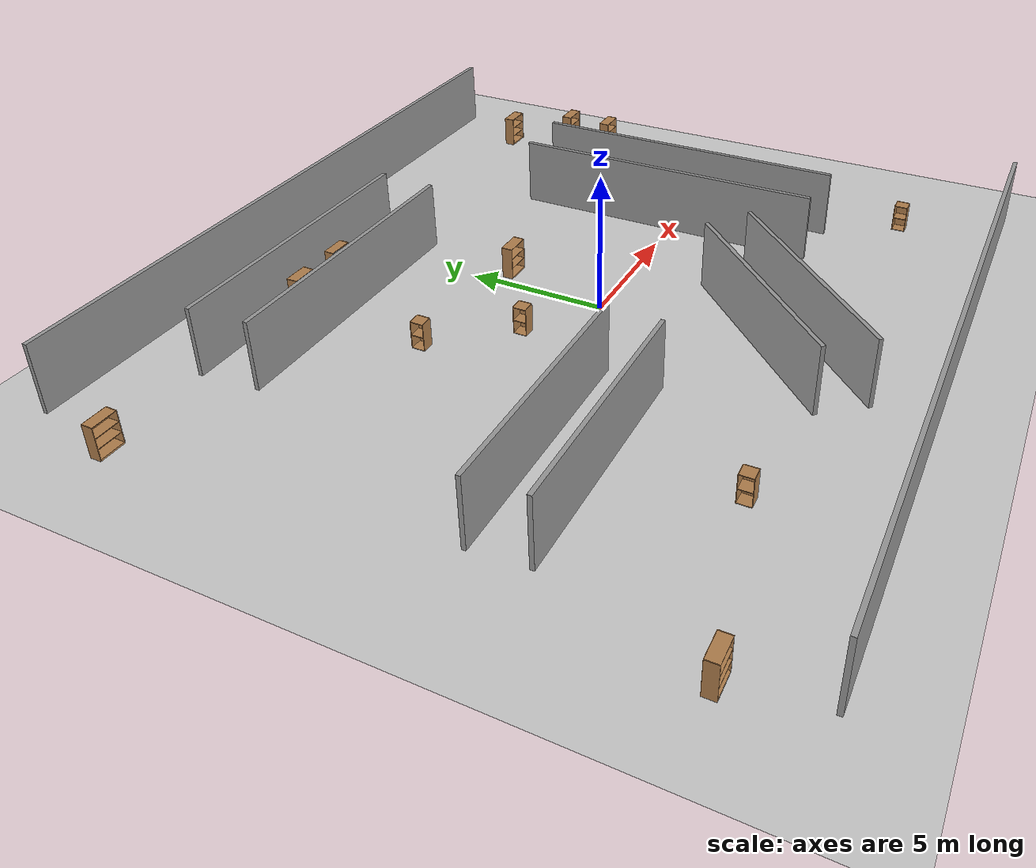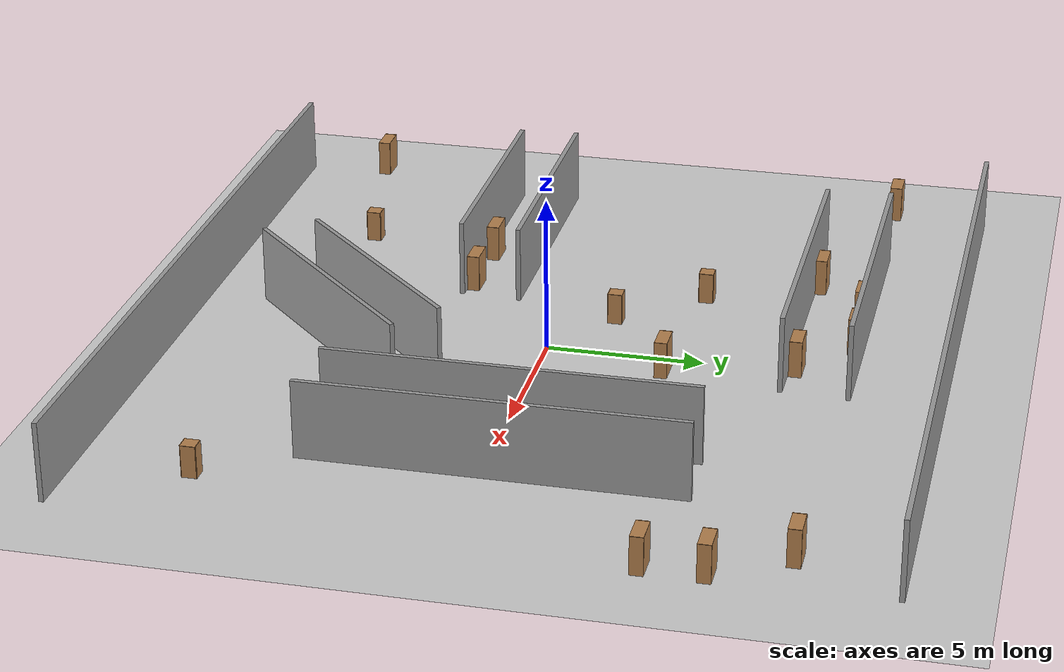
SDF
<sdf version="1.6">
 <world name="default">
  <light name="sun" type="directional">
   <pose>0 0 10 0 -0 0</pose>
   <diffuse>0.8 0.8 0.8 1</diffuse>
   <specular>0.2 0.2 0.2 1</specular>
   <attenuation>
    <range>1000</range>
    <constant>0.9</constant>
    <linear>0.01</linear>
    <quadratic>0.001</quadratic>
   </attenuation>
   <direction>-0.5 0.1 -0.9</direction>
  </light>
  <model name="ground_plane">
   <static>1</static>
   <link name="link">
    <collision name="collision">
     <geometry><plane><normal>0 0 1</normal><size>100 100</size></plane></geometry>
     <surface><friction><ode><mu>100</mu><mu2>50</mu2></ode></friction></surface>
    </collision>
    <visual name="visual">
     <cast_shadows>0</cast_shadows>
     <geometry><plane><normal>0 0 1</normal><size>100 100</size></plane></geometry>
     <material>
      <script><uri>file://media/materials/scripts/gazebo.material</uri><name>Gazebo/Grey</name></script>
     </material>
    </visual>
   </link>
  </model>
  <gravity>0 0 -9.8</gravity>
  <magnetic_field>6e-06 2.3e-05 -4.2e-05</magnetic_field>
  <atmosphere type="adiabatic"/>
  <physics name="default_physics" default="0" type="ode">
   <max_step_size>0.001</max_step_size>
   <real_time_factor>1</real_time_factor>
   <real_time_update_rate>1000</real_time_update_rate>
  </physics>
  <scene><ambient>0.4 0.4 0.4 1</ambient><background>0.7 0.7 0.7 1</background><shadows>1</shadows></scene>
  <audio><device>default</device></audio>
  <spherical_coordinates>
   <surface_model>EARTH_WGS84</surface_model>
   <latitude_deg>0</latitude_deg>
   <longitude_deg>0</longitude_deg>
   <elevation>0</elevation>
   <heading_deg>0</heading_deg>
  </spherical_coordinates>
  <model name="room12">
   <pose>0.021369 0.452466 0 0 -0 0</pose>
   <link name="Wall_0">
    <collision name="Wall_0_Collision">
     <geometry><box><size>25.25 0.15 2.5</size></box></geometry>
     <pose>0 0 1.25 0 -0 0</pose>
    </collision>
    <visual name="Wall_0_Visual">
     <pose>0 0 1.25 0 -0 0</pose>
     <geometry><box><size>25.25 0.15 2.5</size></box></geometry>
     <material>
      <script><uri>file://media/materials/scripts/gazebo.material</uri><name>Gazebo/Grey</name></script>
      <ambient>1 1 1 1</ambient>
     </material>
     <meta><layer>0</layer></meta>
    </visual>
    <pose>0.133001 12.1297 0 0 -0 0</pose>
   </link>
   <link name="Wall_10">
    <collision name="Wall_10_Collision">
     <geometry><box><size>11.5 0.15 2.5</size></box></geometry>
     <pose>0 0 1.25 0 -0 0</pose>
    </collision>
    <visual name="Wall_10_Visual">
     <pose>0 0 1.25 0 -0 0</pose>
     <geometry><box><size>11.5 0.15 2.5</size></box></geometry>
     <material>
      <script><uri>file://media/materials/scripts/gazebo.material</uri><name>Gazebo/Grey</name></script>
      <ambient>1 1 1 1</ambient>
     </material>
     <meta><layer>0</layer></meta>
    </visual>
    <pose>6.38934 -0.088959 0 0 -0 -1.5708</pose>
   </link>
   <link name="Wall_12">
    <collision name="Wall_12_Collision">
     <geometry><box><size>10.25 0.15 2.5</size></box></geometry>
     <pose>0 0 1.25 0 -0 0</pose>
    </collision>
    <visual name="Wall_12_Visual">
     <pose>0 0 1.25 0 -0 0</pose>
     <geometry><box><size>10.25 0.15 2.5</size></box></geometry>
     <material>
      <script><uri>file://media/materials/scripts/gazebo.material</uri><name>Gazebo/Grey</name></script>
      <ambient>1 1 1 1</ambient>
     </material>
     <meta><layer>0</layer></meta>
    </visual>
    <pose>-3.72277 7.15545 0 0 -0 0</pose>
   </link>
   <link name="Wall_14">
    <collision name="Wall_14_Collision">
     <geometry><box><size>8.5 0.15 2.5</size></box></geometry>
     <pose>0 0 1.25 0 -0 0</pose>
    </collision>
    <visual name="Wall_14_Visual">
     <pose>0 0 1.25 0 -0 0</pose>
     <geometry><box><size>8.5 0.15 2.5</size></box></geometry>
     <material>
      <script><uri>file://media/materials/scripts/gazebo.material</uri><name>Gazebo/Grey</name></script>
      <ambient>1 1 1 1</ambient>
     </material>
     <meta><layer>0</layer></meta>
    </visual>
    <pose>-7.60359 -4.06983 0 0 -0 0</pose>
   </link>
   <link name="Wall_16">
    <collision name="Wall_16_Collision">
     <geometry><box><size>8.5 0.15 2.5</size></box></geometry>
     <pose>0 0 1.25 0 -0 0</pose>
    </collision>
    <visual name="Wall_16_Visual">
     <pose>0 0 1.25 0 -0 0</pose>
     <geometry><box><size>8.5 0.15 2.5</size></box></geometry>
     <material>
      <script><uri>file://media/materials/scripts/gazebo.material</uri><name>Gazebo/Grey</name></script>
      <ambient>1 1 1 1</ambient>
     </material>
     <meta><layer>0</layer></meta>
    </visual>
    <pose>1.40858 -7.18858 0 0 -0 0.785398</pose>
   </link>
   <link name="Wall_18">
    <collision name="Wall_18_Collision">
     <geometry><box><size>8 0.15 2.5</size></box></geometry>
     <pose>0 0 1.25 0 -0 0</pose>
    </collision>
    <visual name="Wall_18_Visual">
     <pose>0 0 1.25 0 -0 0</pose>
     <geometry><box><size>8 0.15 2.5</size></box></geometry>
     <material>
      <script><uri>file://media/materials/scripts/gazebo.material</uri><name>Gazebo/Grey</name></script>
      <ambient>1 1 1 1</ambient>
     </material>
     <meta><layer>0</layer></meta>
    </visual>
    <pose>0.158367 -5.93837 0 0 -0 0.785398</pose>
   </link>
   <link name="Wall_2">
    <collision name="Wall_2_Collision">
     <geometry><box><size>10.5 0.15 2.5</size></box></geometry>
     <pose>0 0 1.25 0 -0 0</pose>
    </collision>
    <visual name="Wall_2_Visual">
     <pose>0 0 1.25 0 -0 0</pose>
     <geometry><box><size>10.5 0.15 2.5</size></box></geometry>
     <material>
      <script><uri>file://media/materials/scripts/gazebo.material</uri><name>Gazebo/Grey</name></script>
      <ambient>1 1 1 1</ambient>
     </material>
     <meta><layer>0</layer></meta>
    </visual>
    <pose>-3.75737 9.25687 0 0 -0 0</pose>
   </link>
   <link name="Wall_4">
    <collision name="Wall_4_Collision">
     <geometry><box><size>8.75 0.15 2.5</size></box></geometry>
     <pose>0 0 1.25 0 -0 0</pose>
    </collision>
    <visual name="Wall_4_Visual">
     <pose>0 0 1.25 0 -0 0</pose>
     <geometry><box><size>8.75 0.15 2.5</size></box></geometry>
     <material>
      <script><uri>file://media/materials/scripts/gazebo.material</uri><name>Gazebo/Grey</name></script>
      <ambient>1 1 1 1</ambient>
     </material>
     <meta><layer>0</layer></meta>
    </visual>
    <pose>-7.6116 -2.15462 0 0 -0 0</pose>
   </link>
   <link name="Wall_6">
    <collision name="Wall_6_Collision">
     <geometry><box><size>25.5 0.15 2.5</size></box></geometry>
     <pose>0 0 1.25 0 -0 0</pose>
    </collision>
    <visual name="Wall_6_Visual">
     <pose>0 0 1.25 0 -0 0</pose>
     <geometry><box><size>25.5 0.15 2.5</size></box></geometry>
     <material>
      <script><uri>file://media/materials/scripts/gazebo.material</uri><name>Gazebo/Grey</name></script>
      <ambient>1 1 1 1</ambient>
     </material>
     <meta><layer>0</layer></meta>
    </visual>
    <pose>-0.008001 -12.1297 0 0 -0 0</pose>
   </link>
   <link name="Wall_8">
    <collision name="Wall_8_Collision">
     <geometry><box><size>11.75 0.15 2.5</size></box></geometry>
     <pose>0 0 1.25 0 -0 0</pose>
    </collision>
    <visual name="Wall_8_Visual">
     <pose>0 0 1.25 0 -0 0</pose>
     <geometry><box><size>11.75 0.15 2.5</size></box></geometry>
     <material>
      <script><uri>file://media/materials/scripts/gazebo.material</uri><name>Gazebo/Grey</name></script>
      <ambient>1 1 1 1</ambient>
     </material>
     <meta><layer>0</layer></meta>
    </visual>
    <pose>8.59716 -0.134158 0 0 -0 -1.5708</pose>
   </link>
   <static>1</static>
  </model>
  <model name="bookshelf">
   <static>1</static>
   <link name="link">
    <inertial><mass>1</mass></inertial>
    <collision name="back">
     <pose>0 0.005 0.6 0 -0 0</pose>
     <geometry><box><size>0.9 0.01 1.2</size></box></geometry>
    </collision>
    <visual name="visual1">
     <pose>0 0.005 0.6 0 -0 0</pose>
     <geometry><box><size>0.9 0.01 1.2</size></box></geometry>
     <material>
      <script><uri>file://media/materials/scripts/gazebo.material</uri><name>Gazebo/Wood</name></script>
     </material>
    </visual>
    <collision name="left_side">
     <pose>0.45 -0.195 0.6 0 -0 0</pose>
     <geometry><box><size>0.02 0.4 1.2</size></box></geometry>
    </collision>
    <visual name="visual2">
     <pose>0.45 -0.195 0.6 0 -0 0</pose>
     <geometry><box><size>0.02 0.4 1.2</size></box></geometry>
     <material>
      <script><uri>file://media/materials/scripts/gazebo.material</uri><name>Gazebo/Wood</name></script>
     </material>
    </visual>
    <collision name="right_side">
     <pose>-0.45 -0.195 0.6 0 -0 0</pose>
     <geometry><box><size>0.02 0.4 1.2</size></box></geometry>
    </collision>
    <visual name="visual3">
     <pose>-0.45 -0.195 0.6 0 -0 0</pose>
     <geometry><box><size>0.02 0.4 1.2</size></box></geometry>
     <material>
      <script><uri>file://media/materials/scripts/gazebo.material</uri><name>Gazebo/Wood</name></script>
     </material>
    </visual>
    <collision name="bottom">
     <pose>0 -0.195 0.03 0 -0 0</pose>
     <geometry><box><size>0.88 0.4 0.06</size></box></geometry>
    </collision>
    <visual name="visual4">
     <pose>0 -0.195 0.03 0 -0 0</pose>
     <geometry><box><size>0.88 0.4 0.06</size></box></geometry>
     <material>
      <script><uri>file://media/materials/scripts/gazebo.material</uri><name>Gazebo/Wood</name></script>
     </material>
    </visual>
    <collision name="top">
     <pose>0 -0.195 1.19 0 -0 0</pose>
     <geometry><box><size>0.88 0.4 0.02</size></box></geometry>
    </collision>
    <visual name="visual5">
     <pose>0 -0.195 1.19 0 -0 0</pose>
     <geometry><box><size>0.88 0.4 0.02</size></box></geometry>
     <material>
      <script><uri>file://media/materials/scripts/gazebo.material</uri><name>Gazebo/Wood</name></script>
     </material>
    </visual>
    <collision name="low_shelf">
     <pose>0 -0.195 0.43 0 -0 0</pose>
     <geometry><box><size>0.88 0.4 0.02</size></box></geometry>
    </collision>
    <visual name="visual6">
     <pose>0 -0.195 0.43 0 -0 0</pose>
     <geometry><box><size>0.88 0.4 0.02</size></box></geometry>
     <material>
      <script><uri>file://media/materials/scripts/gazebo.material</uri><name>Gazebo/Wood</name></script>
     </material>
    </visual>
    <collision name="high_shelf">
     <pose>0 -0.195 0.8 0 -0 0</pose>
     <geometry><box><size>0.88 0.4 0.02</size></box></geometry>
    </collision>
    <visual name="visual7">
     <pose>0 -0.195 0.8 0 -0 0</pose>
     <geometry><box><size>0.88 0.4 0.02</size></box></geometry>
     <material>
      <script><uri>file://media/materials/scripts/gazebo.material</uri><name>Gazebo/Wood</name></script>
     </material>
    </visual>
   </link>
   <pose>11.2227 9.72643 0 0 -0 0</pose>
  </model>
  <model name="bookshelf_0">
   <static>1</static>
   <link name="link">
    <inertial><mass>1</mass></inertial>
    <collision name="back">
     <pose>0 0.005 0.6 0 -0 0</pose>
     <geometry><box><size>0.9 0.01 1.2</size></box></geometry>
    </collision>
    <visual name="visual1">
     <pose>0 0.005 0.6 0 -0 0</pose>
     <geometry><box><size>0.9 0.01 1.2</size></box></geometry>
     <material>
      <script><uri>file://media/materials/scripts/gazebo.material</uri><name>Gazebo/Wood</name></script>
     </material>
    </visual>
    <collision name="left_side">
     <pose>0.45 -0.195 0.6 0 -0 0</pose>
     <geometry><box><size>0.02 0.4 1.2</size></box></geometry>
    </collision>
    <visual name="visual2">
     <pose>0.45 -0.195 0.6 0 -0 0</pose>
     <geometry><box><size>0.02 0.4 1.2</size></box></geometry>
     <material>
      <script><uri>file://media/materials/scripts/gazebo.material</uri><name>Gazebo/Wood</name></script>
     </material>
    </visual>
    <collision name="right_side">
     <pose>-0.45 -0.195 0.6 0 -0 0</pose>
     <geometry><box><size>0.02 0.4 1.2</size></box></geometry>
    </collision>
    <visual name="visual3">
     <pose>-0.45 -0.195 0.6 0 -0 0</pose>
     <geometry><box><size>0.02 0.4 1.2</size></box></geometry>
     <material>
      <script><uri>file://media/materials/scripts/gazebo.material</uri><name>Gazebo/Wood</name></script>
     </material>
    </visual>
    <collision name="bottom">
     <pose>0 -0.195 0.03 0 -0 0</pose>
     <geometry><box><size>0.88 0.4 0.06</size></box></geometry>
    </collision>
    <visual name="visual4">
     <pose>0 -0.195 0.03 0 -0 0</pose>
     <geometry><box><size>0.88 0.4 0.06</size></box></geometry>
     <material>
      <script><uri>file://media/materials/scripts/gazebo.material</uri><name>Gazebo/Wood</name></script>
     </material>
    </visual>
    <collision name="top">
     <pose>0 -0.195 1.19 0 -0 0</pose>
     <geometry><box><size>0.88 0.4 0.02</size></box></geometry>
    </collision>
    <visual name="visual5">
     <pose>0 -0.195 1.19 0 -0 0</pose>
     <geometry><box><size>0.88 0.4 0.02</size></box></geometry>
     <material>
      <script><uri>file://media/materials/scripts/gazebo.material</uri><name>Gazebo/Wood</name></script>
     </material>
    </visual>
    <collision name="low_shelf">
     <pose>0 -0.195 0.43 0 -0 0</pose>
     <geometry><box><size>0.88 0.4 0.02</size></box></geometry>
    </collision>
    <visual name="visual6">
     <pose>0 -0.195 0.43 0 -0 0</pose>
     <geometry><box><size>0.88 0.4 0.02</size></box></geometry>
     <material>
      <script><uri>file://media/materials/scripts/gazebo.material</uri><name>Gazebo/Wood</name></script>
     </material>
    </visual>
    <collision name="high_shelf">
     <pose>0 -0.195 0.8 0 -0 0</pose>
     <geometry><box><size>0.88 0.4 0.02</size></box></geometry>
    </collision>
    <visual name="visual7">
     <pose>0 -0.195 0.8 0 -0 0</pose>
     <geometry><box><size>0.88 0.4 0.02</size></box></geometry>
     <material>
      <script><uri>file://media/materials/scripts/gazebo.material</uri><name>Gazebo/Wood</name></script>
     </material>
    </visual>
   </link>
   <pose>12.5461 7.50087 0 0 -0 0</pose>
  </model>
  <model name="bookshelf_1">
   <static>1</static>
   <link name="link">
    <inertial><mass>1</mass></inertial>
    <collision name="back">
     <pose>0 0.005 0.6 0 -0 0</pose>
     <geometry><box><size>0.9 0.01 1.2</size></box></geometry>
    </collision>
    <visual name="visual1">
     <pose>0 0.005 0.6 0 -0 0</pose>
     <geometry><box><size>0.9 0.01 1.2</size></box></geometry>
     <material>
      <script><uri>file://media/materials/scripts/gazebo.material</uri><name>Gazebo/Wood</name></script>
     </material>
    </visual>
    <collision name="left_side">
     <pose>0.45 -0.195 0.6 0 -0 0</pose>
     <geometry><box><size>0.02 0.4 1.2</size></box></geometry>
    </collision>
    <visual name="visual2">
     <pose>0.45 -0.195 0.6 0 -0 0</pose>
     <geometry><box><size>0.02 0.4 1.2</size></box></geometry>
     <material>
      <script><uri>file://media/materials/scripts/gazebo.material</uri><name>Gazebo/Wood</name></script>
     </material>
    </visual>
    <collision name="right_side">
     <pose>-0.45 -0.195 0.6 0 -0 0</pose>
     <geometry><box><size>0.02 0.4 1.2</size></box></geometry>
    </collision>
    <visual name="visual3">
     <pose>-0.45 -0.195 0.6 0 -0 0</pose>
     <geometry><box><size>0.02 0.4 1.2</size></box></geometry>
     <material>
      <script><uri>file://media/materials/scripts/gazebo.material</uri><name>Gazebo/Wood</name></script>
     </material>
    </visual>
    <collision name="bottom">
     <pose>0 -0.195 0.03 0 -0 0</pose>
     <geometry><box><size>0.88 0.4 0.06</size></box></geometry>
    </collision>
    <visual name="visual4">
     <pose>0 -0.195 0.03 0 -0 0</pose>
     <geometry><box><size>0.88 0.4 0.06</size></box></geometry>
     <material>
      <script><uri>file://media/materials/scripts/gazebo.material</uri><name>Gazebo/Wood</name></script>
     </material>
    </visual>
    <collision name="top">
     <pose>0 -0.195 1.19 0 -0 0</pose>
     <geometry><box><size>0.88 0.4 0.02</size></box></geometry>
    </collision>
    <visual name="visual5">
     <pose>0 -0.195 1.19 0 -0 0</pose>
     <geometry><box><size>0.88 0.4 0.02</size></box></geometry>
     <material>
      <script><uri>file://media/materials/scripts/gazebo.material</uri><name>Gazebo/Wood</name></script>
     </material>
    </visual>
    <collision name="low_shelf">
     <pose>0 -0.195 0.43 0 -0 0</pose>
     <geometry><box><size>0.88 0.4 0.02</size></box></geometry>
    </collision>
    <visual name="visual6">
     <pose>0 -0.195 0.43 0 -0 0</pose>
     <geometry><box><size>0.88 0.4 0.02</size></box></geometry>
     <material>
      <script><uri>file://media/materials/scripts/gazebo.material</uri><name>Gazebo/Wood</name></script>
     </material>
    </visual>
    <collision name="high_shelf">
     <pose>0 -0.195 0.8 0 -0 0</pose>
     <geometry><box><size>0.88 0.4 0.02</size></box></geometry>
    </collision>
    <visual name="visual7">
     <pose>0 -0.195 0.8 0 -0 0</pose>
     <geometry><box><size>0.88 0.4 0.02</size></box></geometry>
     <material>
      <script><uri>file://media/materials/scripts/gazebo.material</uri><name>Gazebo/Wood</name></script>
     </material>
    </visual>
   </link>
   <pose>12.5496 5.66017 0 0 -0 0</pose>
  </model>
  <model name="bookshelf_2">
   <static>1</static>
   <link name="link">
    <inertial><mass>1</mass></inertial>
    <collision name="back">
     <pose>0 0.005 0.6 0 -0 0</pose>
     <geometry><box><size>0.9 0.01 1.2</size></box></geometry>
    </collision>
    <visual name="visual1">
     <pose>0 0.005 0.6 0 -0 0</pose>
     <geometry><box><size>0.9 0.01 1.2</size></box></geometry>
     <material>
      <script><uri>file://media/materials/scripts/gazebo.material</uri><name>Gazebo/Wood</name></script>
     </material>
    </visual>
    <collision name="left_side">
     <pose>0.45 -0.195 0.6 0 -0 0</pose>
     <geometry><box><size>0.02 0.4 1.2</size></box></geometry>
    </collision>
    <visual name="visual2">
     <pose>0.45 -0.195 0.6 0 -0 0</pose>
     <geometry><box><size>0.02 0.4 1.2</size></box></geometry>
     <material>
      <script><uri>file://media/materials/scripts/gazebo.material</uri><name>Gazebo/Wood</name></script>
     </material>
    </visual>
    <collision name="right_side">
     <pose>-0.45 -0.195 0.6 0 -0 0</pose>
     <geometry><box><size>0.02 0.4 1.2</size></box></geometry>
    </collision>
    <visual name="visual3">
     <pose>-0.45 -0.195 0.6 0 -0 0</pose>
     <geometry><box><size>0.02 0.4 1.2</size></box></geometry>
     <material>
      <script><uri>file://media/materials/scripts/gazebo.material</uri><name>Gazebo/Wood</name></script>
     </material>
    </visual>
    <collision name="bottom">
     <pose>0 -0.195 0.03 0 -0 0</pose>
     <geometry><box><size>0.88 0.4 0.06</size></box></geometry>
    </collision>
    <visual name="visual4">
     <pose>0 -0.195 0.03 0 -0 0</pose>
     <geometry><box><size>0.88 0.4 0.06</size></box></geometry>
     <material>
      <script><uri>file://media/materials/scripts/gazebo.material</uri><name>Gazebo/Wood</name></script>
     </material>
    </visual>
    <collision name="top">
     <pose>0 -0.195 1.19 0 -0 0</pose>
     <geometry><box><size>0.88 0.4 0.02</size></box></geometry>
    </collision>
    <visual name="visual5">
     <pose>0 -0.195 1.19 0 -0 0</pose>
     <geometry><box><size>0.88 0.4 0.02</size></box></geometry>
     <material>
      <script><uri>file://media/materials/scripts/gazebo.material</uri><name>Gazebo/Wood</name></script>
     </material>
    </visual>
    <collision name="low_shelf">
     <pose>0 -0.195 0.43 0 -0 0</pose>
     <geometry><box><size>0.88 0.4 0.02</size></box></geometry>
    </collision>
    <visual name="visual6">
     <pose>0 -0.195 0.43 0 -0 0</pose>
     <geometry><box><size>0.88 0.4 0.02</size></box></geometry>
     <material>
      <script><uri>file://media/materials/scripts/gazebo.material</uri><name>Gazebo/Wood</name></script>
     </material>
    </visual>
    <collision name="high_shelf">
     <pose>0 -0.195 0.8 0 -0 0</pose>
     <geometry><box><size>0.88 0.4 0.02</size></box></geometry>
    </collision>
    <visual name="visual7">
     <pose>0 -0.195 0.8 0 -0 0</pose>
     <geometry><box><size>0.88 0.4 0.02</size></box></geometry>
     <material>
      <script><uri>file://media/materials/scripts/gazebo.material</uri><name>Gazebo/Wood</name></script>
     </material>
    </visual>
   </link>
   <pose>-12.949 9.74669 0 0 -0 0</pose>
  </model>
  <model name="bookshelf_3">
   <static>1</static>
   <link name="link">
    <inertial><mass>1</mass></inertial>
    <collision name="back">
     <pose>0 0.005 0.6 0 -0 0</pose>
     <geometry><box><size>0.9 0.01 1.2</size></box></geometry>
    </collision>
    <visual name="visual1">
     <pose>0 0.005 0.6 0 -0 0</pose>
     <geometry><box><size>0.9 0.01 1.2</size></box></geometry>
     <material>
      <script><uri>file://media/materials/scripts/gazebo.material</uri><name>Gazebo/Wood</name></script>
     </material>
    </visual>
    <collision name="left_side">
     <pose>0.45 -0.195 0.6 0 -0 0</pose>
     <geometry><box><size>0.02 0.4 1.2</size></box></geometry>
    </collision>
    <visual name="visual2">
     <pose>0.45 -0.195 0.6 0 -0 0</pose>
     <geometry><box><size>0.02 0.4 1.2</size></box></geometry>
     <material>
      <script><uri>file://media/materials/scripts/gazebo.material</uri><name>Gazebo/Wood</name></script>
     </material>
    </visual>
    <collision name="right_side">
     <pose>-0.45 -0.195 0.6 0 -0 0</pose>
     <geometry><box><size>0.02 0.4 1.2</size></box></geometry>
    </collision>
    <visual name="visual3">
     <pose>-0.45 -0.195 0.6 0 -0 0</pose>
     <geometry><box><size>0.02 0.4 1.2</size></box></geometry>
     <material>
      <script><uri>file://media/materials/scripts/gazebo.material</uri><name>Gazebo/Wood</name></script>
     </material>
    </visual>
    <collision name="bottom">
     <pose>0 -0.195 0.03 0 -0 0</pose>
     <geometry><box><size>0.88 0.4 0.06</size></box></geometry>
    </collision>
    <visual name="visual4">
     <pose>0 -0.195 0.03 0 -0 0</pose>
     <geometry><box><size>0.88 0.4 0.06</size></box></geometry>
     <material>
      <script><uri>file://media/materials/scripts/gazebo.material</uri><name>Gazebo/Wood</name></script>
     </material>
    </visual>
    <collision name="top">
     <pose>0 -0.195 1.19 0 -0 0</pose>
     <geometry><box><size>0.88 0.4 0.02</size></box></geometry>
    </collision>
    <visual name="visual5">
     <pose>0 -0.195 1.19 0 -0 0</pose>
     <geometry><box><size>0.88 0.4 0.02</size></box></geometry>
     <material>
      <script><uri>file://media/materials/scripts/gazebo.material</uri><name>Gazebo/Wood</name></script>
     </material>
    </visual>
    <collision name="low_shelf">
     <pose>0 -0.195 0.43 0 -0 0</pose>
     <geometry><box><size>0.88 0.4 0.02</size></box></geometry>
    </collision>
    <visual name="visual6">
     <pose>0 -0.195 0.43 0 -0 0</pose>
     <geometry><box><size>0.88 0.4 0.02</size></box></geometry>
     <material>
      <script><uri>file://media/materials/scripts/gazebo.material</uri><name>Gazebo/Wood</name></script>
     </material>
    </visual>
    <collision name="high_shelf">
     <pose>0 -0.195 0.8 0 -0 0</pose>
     <geometry><box><size>0.88 0.4 0.02</size></box></geometry>
    </collision>
    <visual name="visual7">
     <pose>0 -0.195 0.8 0 -0 0</pose>
     <geometry><box><size>0.88 0.4 0.02</size></box></geometry>
     <material>
      <script><uri>file://media/materials/scripts/gazebo.material</uri><name>Gazebo/Wood</name></script>
     </material>
    </visual>
   </link>
   <pose>-13.0933 -8.75645 0 0 -0 0</pose>
  </model>
  <model name="bookshelf_4">
   <static>1</static>
   <link name="link">
    <inertial><mass>1</mass></inertial>
    <collision name="back">
     <pose>0 0.005 0.6 0 -0 0</pose>
     <geometry><box><size>0.9 0.01 1.2</size></box></geometry>
    </collision>
    <visual name="visual1">
     <pose>0 0.005 0.6 0 -0 0</pose>
     <geometry><box><size>0.9 0.01 1.2</size></box></geometry>
     <material>
      <script><uri>file://media/materials/scripts/gazebo.material</uri><name>Gazebo/Wood</name></script>
     </material>
    </visual>
    <collision name="left_side">
     <pose>0.45 -0.195 0.6 0 -0 0</pose>
     <geometry><box><size>0.02 0.4 1.2</size></box></geometry>
    </collision>
    <visual name="visual2">
     <pose>0.45 -0.195 0.6 0 -0 0</pose>
     <geometry><box><size>0.02 0.4 1.2</size></box></geometry>
     <material>
      <script><uri>file://media/materials/scripts/gazebo.material</uri><name>Gazebo/Wood</name></script>
     </material>
    </visual>
    <collision name="right_side">
     <pose>-0.45 -0.195 0.6 0 -0 0</pose>
     <geometry><box><size>0.02 0.4 1.2</size></box></geometry>
    </collision>
    <visual name="visual3">
     <pose>-0.45 -0.195 0.6 0 -0 0</pose>
     <geometry><box><size>0.02 0.4 1.2</size></box></geometry>
     <material>
      <script><uri>file://media/materials/scripts/gazebo.material</uri><name>Gazebo/Wood</name></script>
     </material>
    </visual>
    <collision name="bottom">
     <pose>0 -0.195 0.03 0 -0 0</pose>
     <geometry><box><size>0.88 0.4 0.06</size></box></geometry>
    </collision>
    <visual name="visual4">
     <pose>0 -0.195 0.03 0 -0 0</pose>
     <geometry><box><size>0.88 0.4 0.06</size></box></geometry>
     <material>
      <script><uri>file://media/materials/scripts/gazebo.material</uri><name>Gazebo/Wood</name></script>
     </material>
    </visual>
    <collision name="top">
     <pose>0 -0.195 1.19 0 -0 0</pose>
     <geometry><box><size>0.88 0.4 0.02</size></box></geometry>
    </collision>
    <visual name="visual5">
     <pose>0 -0.195 1.19 0 -0 0</pose>
     <geometry><box><size>0.88 0.4 0.02</size></box></geometry>
     <material>
      <script><uri>file://media/materials/scripts/gazebo.material</uri><name>Gazebo/Wood</name></script>
     </material>
    </visual>
    <collision name="low_shelf">
     <pose>0 -0.195 0.43 0 -0 0</pose>
     <geometry><box><size>0.88 0.4 0.02</size></box></geometry>
    </collision>
    <visual name="visual6">
     <pose>0 -0.195 0.43 0 -0 0</pose>
     <geometry><box><size>0.88 0.4 0.02</size></box></geometry>
     <material>
      <script><uri>file://media/materials/scripts/gazebo.material</uri><name>Gazebo/Wood</name></script>
     </material>
    </visual>
    <collision name="high_shelf">
     <pose>0 -0.195 0.8 0 -0 0</pose>
     <geometry><box><size>0.88 0.4 0.02</size></box></geometry>
    </collision>
    <visual name="visual7">
     <pose>0 -0.195 0.8 0 -0 0</pose>
     <geometry><box><size>0.88 0.4 0.02</size></box></geometry>
     <material>
      <script><uri>file://media/materials/scripts/gazebo.material</uri><name>Gazebo/Wood</name></script>
     </material>
    </visual>
   </link>
   <pose>0.857474 4.07096 0 0 -0 0</pose>
  </model>
  <model name="bookshelf_5">
   <static>1</static>
   <link name="link">
    <inertial><mass>1</mass></inertial>
    <collision name="back">
     <pose>0 0.005 0.6 0 -0 0</pose>
     <geometry><box><size>0.9 0.01 1.2</size></box></geometry>
    </collision>
    <visual name="visual1">
     <pose>0 0.005 0.6 0 -0 0</pose>
     <geometry><box><size>0.9 0.01 1.2</size></box></geometry>
     <material>
      <script><uri>file://media/materials/scripts/gazebo.material</uri><name>Gazebo/Wood</name></script>
     </material>
    </visual>
    <collision name="left_side">
     <pose>0.45 -0.195 0.6 0 -0 0</pose>
     <geometry><box><size>0.02 0.4 1.2</size></box></geometry>
    </collision>
    <visual name="visual2">
     <pose>0.45 -0.195 0.6 0 -0 0</pose>
     <geometry><box><size>0.02 0.4 1.2</size></box></geometry>
     <material>
      <script><uri>file://media/materials/scripts/gazebo.material</uri><name>Gazebo/Wood</name></script>
     </material>
    </visual>
    <collision name="right_side">
     <pose>-0.45 -0.195 0.6 0 -0 0</pose>
     <geometry><box><size>0.02 0.4 1.2</size></box></geometry>
    </collision>
    <visual name="visual3">
     <pose>-0.45 -0.195 0.6 0 -0 0</pose>
     <geometry><box><size>0.02 0.4 1.2</size></box></geometry>
     <material>
      <script><uri>file://media/materials/scripts/gazebo.material</uri><name>Gazebo/Wood</name></script>
     </material>
    </visual>
    <collision name="bottom">
     <pose>0 -0.195 0.03 0 -0 0</pose>
     <geometry><box><size>0.88 0.4 0.06</size></box></geometry>
    </collision>
    <visual name="visual4">
     <pose>0 -0.195 0.03 0 -0 0</pose>
     <geometry><box><size>0.88 0.4 0.06</size></box></geometry>
     <material>
      <script><uri>file://media/materials/scripts/gazebo.material</uri><name>Gazebo/Wood</name></script>
     </material>
    </visual>
    <collision name="top">
     <pose>0 -0.195 1.19 0 -0 0</pose>
     <geometry><box><size>0.88 0.4 0.02</size></box></geometry>
    </collision>
    <visual name="visual5">
     <pose>0 -0.195 1.19 0 -0 0</pose>
     <geometry><box><size>0.88 0.4 0.02</size></box></geometry>
     <material>
      <script><uri>file://media/materials/scripts/gazebo.material</uri><name>Gazebo/Wood</name></script>
     </material>
    </visual>
    <collision name="low_shelf">
     <pose>0 -0.195 0.43 0 -0 0</pose>
     <geometry><box><size>0.88 0.4 0.02</size></box></geometry>
    </collision>
    <visual name="visual6">
     <pose>0 -0.195 0.43 0 -0 0</pose>
     <geometry><box><size>0.88 0.4 0.02</size></box></geometry>
     <material>
      <script><uri>file://media/materials/scripts/gazebo.material</uri><name>Gazebo/Wood</name></script>
     </material>
    </visual>
    <collision name="high_shelf">
     <pose>0 -0.195 0.8 0 -0 0</pose>
     <geometry><box><size>0.88 0.4 0.02</size></box></geometry>
    </collision>
    <visual name="visual7">
     <pose>0 -0.195 0.8 0 -0 0</pose>
     <geometry><box><size>0.88 0.4 0.02</size></box></geometry>
     <material>
      <script><uri>file://media/materials/scripts/gazebo.material</uri><name>Gazebo/Wood</name></script>
     </material>
    </visual>
   </link>
   <pose>-4.10204 -3.13024 0 0 -0 0</pose>
  </model>
  <model name="bookshelf_6">
   <static>1</static>
   <link name="link">
    <inertial><mass>1</mass></inertial>
    <collision name="back">
     <pose>0 0.005 0.6 0 -0 0</pose>
     <geometry><box><size>0.9 0.01 1.2</size></box></geometry>
    </collision>
    <visual name="visual1">
     <pose>0 0.005 0.6 0 -0 0</pose>
     <geometry><box><size>0.9 0.01 1.2</size></box></geometry>
     <material>
      <script><uri>file://media/materials/scripts/gazebo.material</uri><name>Gazebo/Wood</name></script>
     </material>
    </visual>
    <collision name="left_side">
     <pose>0.45 -0.195 0.6 0 -0 0</pose>
     <geometry><box><size>0.02 0.4 1.2</size></box></geometry>
    </collision>
    <visual name="visual2">
     <pose>0.45 -0.195 0.6 0 -0 0</pose>
     <geometry><box><size>0.02 0.4 1.2</size></box></geometry>
     <material>
      <script><uri>file://media/materials/scripts/gazebo.material</uri><name>Gazebo/Wood</name></script>
     </material>
    </visual>
    <collision name="right_side">
     <pose>-0.45 -0.195 0.6 0 -0 0</pose>
     <geometry><box><size>0.02 0.4 1.2</size></box></geometry>
    </collision>
    <visual name="visual3">
     <pose>-0.45 -0.195 0.6 0 -0 0</pose>
     <geometry><box><size>0.02 0.4 1.2</size></box></geometry>
     <material>
      <script><uri>file://media/materials/scripts/gazebo.material</uri><name>Gazebo/Wood</name></script>
     </material>
    </visual>
    <collision name="bottom">
     <pose>0 -0.195 0.03 0 -0 0</pose>
     <geometry><box><size>0.88 0.4 0.06</size></box></geometry>
    </collision>
    <visual name="visual4">
     <pose>0 -0.195 0.03 0 -0 0</pose>
     <geometry><box><size>0.88 0.4 0.06</size></box></geometry>
     <material>
      <script><uri>file://media/materials/scripts/gazebo.material</uri><name>Gazebo/Wood</name></script>
     </material>
    </visual>
    <collision name="top">
     <pose>0 -0.195 1.19 0 -0 0</pose>
     <geometry><box><size>0.88 0.4 0.02</size></box></geometry>
    </collision>
    <visual name="visual5">
     <pose>0 -0.195 1.19 0 -0 0</pose>
     <geometry><box><size>0.88 0.4 0.02</size></box></geometry>
     <material>
      <script><uri>file://media/materials/scripts/gazebo.material</uri><name>Gazebo/Wood</name></script>
     </material>
    </visual>
    <collision name="low_shelf">
     <pose>0 -0.195 0.43 0 -0 0</pose>
     <geometry><box><size>0.88 0.4 0.02</size></box></geometry>
    </collision>
    <visual name="visual6">
     <pose>0 -0.195 0.43 0 -0 0</pose>
     <geometry><box><size>0.88 0.4 0.02</size></box></geometry>
     <material>
      <script><uri>file://media/materials/scripts/gazebo.material</uri><name>Gazebo/Wood</name></script>
     </material>
    </visual>
    <collision name="high_shelf">
     <pose>0 -0.195 0.8 0 -0 0</pose>
     <geometry><box><size>0.88 0.4 0.02</size></box></geometry>
    </collision>
    <visual name="visual7">
     <pose>0 -0.195 0.8 0 -0 0</pose>
     <geometry><box><size>0.88 0.4 0.02</size></box></geometry>
     <material>
      <script><uri>file://media/materials/scripts/gazebo.material</uri><name>Gazebo/Wood</name></script>
     </material>
    </visual>
   </link>
   <pose>-6.59444 -3.08849 0 0 -0 0</pose>
  </model>
  <model name="bookshelf_7">
   <static>1</static>
   <link name="link">
    <inertial><mass>1</mass></inertial>
    <collision name="back">
     <pose>0 0.005 0.6 0 -0 0</pose>
     <geometry><box><size>0.9 0.01 1.2</size></box></geometry>
    </collision>
    <visual name="visual1">
     <pose>0 0.005 0.6 0 -0 0</pose>
     <geometry><box><size>0.9 0.01 1.2</size></box></geometry>
     <material>
      <script><uri>file://media/materials/scripts/gazebo.material</uri><name>Gazebo/Wood</name></script>
     </material>
    </visual>
    <collision name="left_side">
     <pose>0.45 -0.195 0.6 0 -0 0</pose>
     <geometry><box><size>0.02 0.4 1.2</size></box></geometry>
    </collision>
    <visual name="visual2">
     <pose>0.45 -0.195 0.6 0 -0 0</pose>
     <geometry><box><size>0.02 0.4 1.2</size></box></geometry>
     <material>
      <script><uri>file://media/materials/scripts/gazebo.material</uri><name>Gazebo/Wood</name></script>
     </material>
    </visual>
    <collision name="right_side">
     <pose>-0.45 -0.195 0.6 0 -0 0</pose>
     <geometry><box><size>0.02 0.4 1.2</size></box></geometry>
    </collision>
    <visual name="visual3">
     <pose>-0.45 -0.195 0.6 0 -0 0</pose>
     <geometry><box><size>0.02 0.4 1.2</size></box></geometry>
     <material>
      <script><uri>file://media/materials/scripts/gazebo.material</uri><name>Gazebo/Wood</name></script>
     </material>
    </visual>
    <collision name="bottom">
     <pose>0 -0.195 0.03 0 -0 0</pose>
     <geometry><box><size>0.88 0.4 0.06</size></box></geometry>
    </collision>
    <visual name="visual4">
     <pose>0 -0.195 0.03 0 -0 0</pose>
     <geometry><box><size>0.88 0.4 0.06</size></box></geometry>
     <material>
      <script><uri>file://media/materials/scripts/gazebo.material</uri><name>Gazebo/Wood</name></script>
     </material>
    </visual>
    <collision name="top">
     <pose>0 -0.195 1.19 0 -0 0</pose>
     <geometry><box><size>0.88 0.4 0.02</size></box></geometry>
    </collision>
    <visual name="visual5">
     <pose>0 -0.195 1.19 0 -0 0</pose>
     <geometry><box><size>0.88 0.4 0.02</size></box></geometry>
     <material>
      <script><uri>file://media/materials/scripts/gazebo.material</uri><name>Gazebo/Wood</name></script>
     </material>
    </visual>
    <collision name="low_shelf">
     <pose>0 -0.195 0.43 0 -0 0</pose>
     <geometry><box><size>0.88 0.4 0.02</size></box></geometry>
    </collision>
    <visual name="visual6">
     <pose>0 -0.195 0.43 0 -0 0</pose>
     <geometry><box><size>0.88 0.4 0.02</size></box></geometry>
     <material>
      <script><uri>file://media/materials/scripts/gazebo.material</uri><name>Gazebo/Wood</name></script>
     </material>
    </visual>
    <collision name="high_shelf">
     <pose>0 -0.195 0.8 0 -0 0</pose>
     <geometry><box><size>0.88 0.4 0.02</size></box></geometry>
    </collision>
    <visual name="visual7">
     <pose>0 -0.195 0.8 0 -0 0</pose>
     <geometry><box><size>0.88 0.4 0.02</size></box></geometry>
     <material>
      <script><uri>file://media/materials/scripts/gazebo.material</uri><name>Gazebo/Wood</name></script>
     </material>
    </visual>
   </link>
   <pose>-0.123708 8.10105 0 0 -0 0</pose>
  </model>
  <model name="bookshelf_8">
   <static>1</static>
   <link name="link">
    <inertial><mass>1</mass></inertial>
    <collision name="back">
     <pose>0 0.005 0.6 0 -0 0</pose>
     <geometry><box><size>0.9 0.01 1.2</size></box></geometry>
    </collision>
    <visual name="visual1">
     <pose>0 0.005 0.6 0 -0 0</pose>
     <geometry><box><size>0.9 0.01 1.2</size></box></geometry>
     <material>
      <script><uri>file://media/materials/scripts/gazebo.material</uri><name>Gazebo/Wood</name></script>
     </material>
    </visual>
    <collision name="left_side">
     <pose>0.45 -0.195 0.6 0 -0 0</pose>
     <geometry><box><size>0.02 0.4 1.2</size></box></geometry>
    </collision>
    <visual name="visual2">
     <pose>0.45 -0.195 0.6 0 -0 0</pose>
     <geometry><box><size>0.02 0.4 1.2</size></box></geometry>
     <material>
      <script><uri>file://media/materials/scripts/gazebo.material</uri><name>Gazebo/Wood</name></script>
     </material>
    </visual>
    <collision name="right_side">
     <pose>-0.45 -0.195 0.6 0 -0 0</pose>
     <geometry><box><size>0.02 0.4 1.2</size></box></geometry>
    </collision>
    <visual name="visual3">
     <pose>-0.45 -0.195 0.6 0 -0 0</pose>
     <geometry><box><size>0.02 0.4 1.2</size></box></geometry>
     <material>
      <script><uri>file://media/materials/scripts/gazebo.material</uri><name>Gazebo/Wood</name></script>
     </material>
    </visual>
    <collision name="bottom">
     <pose>0 -0.195 0.03 0 -0 0</pose>
     <geometry><box><size>0.88 0.4 0.06</size></box></geometry>
    </collision>
    <visual name="visual4">
     <pose>0 -0.195 0.03 0 -0 0</pose>
     <geometry><box><size>0.88 0.4 0.06</size></box></geometry>
     <material>
      <script><uri>file://media/materials/scripts/gazebo.material</uri><name>Gazebo/Wood</name></script>
     </material>
    </visual>
    <collision name="top">
     <pose>0 -0.195 1.19 0 -0 0</pose>
     <geometry><box><size>0.88 0.4 0.02</size></box></geometry>
    </collision>
    <visual name="visual5">
     <pose>0 -0.195 1.19 0 -0 0</pose>
     <geometry><box><size>0.88 0.4 0.02</size></box></geometry>
     <material>
      <script><uri>file://media/materials/scripts/gazebo.material</uri><name>Gazebo/Wood</name></script>
     </material>
    </visual>
    <collision name="low_shelf">
     <pose>0 -0.195 0.43 0 -0 0</pose>
     <geometry><box><size>0.88 0.4 0.02</size></box></geometry>
    </collision>
    <visual name="visual6">
     <pose>0 -0.195 0.43 0 -0 0</pose>
     <geometry><box><size>0.88 0.4 0.02</size></box></geometry>
     <material>
      <script><uri>file://media/materials/scripts/gazebo.material</uri><name>Gazebo/Wood</name></script>
     </material>
    </visual>
    <collision name="high_shelf">
     <pose>0 -0.195 0.8 0 -0 0</pose>
     <geometry><box><size>0.88 0.4 0.02</size></box></geometry>
    </collision>
    <visual name="visual7">
     <pose>0 -0.195 0.8 0 -0 0</pose>
     <geometry><box><size>0.88 0.4 0.02</size></box></geometry>
     <material>
      <script><uri>file://media/materials/scripts/gazebo.material</uri><name>Gazebo/Wood</name></script>
     </material>
    </visual>
   </link>
   <pose>-2.06798 9.66867 0 0 -0 0</pose>
  </model>
  <model name="bookshelf_9">
   <static>1</static>
   <link name="link">
    <inertial><mass>1</mass></inertial>
    <collision name="back">
     <pose>0 0.005 0.6 0 -0 0</pose>
     <geometry><box><size>0.9 0.01 1.2</size></box></geometry>
    </collision>
    <visual name="visual1">
     <pose>0 0.005 0.6 0 -0 0</pose>
     <geometry><box><size>0.9 0.01 1.2</size></box></geometry>
     <material>
      <script><uri>file://media/materials/scripts/gazebo.material</uri><name>Gazebo/Wood</name></script>
     </material>
    </visual>
    <collision name="left_side">
     <pose>0.45 -0.195 0.6 0 -0 0</pose>
     <geometry><box><size>0.02 0.4 1.2</size></box></geometry>
    </collision>
    <visual name="visual2">
     <pose>0.45 -0.195 0.6 0 -0 0</pose>
     <geometry><box><size>0.02 0.4 1.2</size></box></geometry>
     <material>
      <script><uri>file://media/materials/scripts/gazebo.material</uri><name>Gazebo/Wood</name></script>
     </material>
    </visual>
    <collision name="right_side">
     <pose>-0.45 -0.195 0.6 0 -0 0</pose>
     <geometry><box><size>0.02 0.4 1.2</size></box></geometry>
    </collision>
    <visual name="visual3">
     <pose>-0.45 -0.195 0.6 0 -0 0</pose>
     <geometry><box><size>0.02 0.4 1.2</size></box></geometry>
     <material>
      <script><uri>file://media/materials/scripts/gazebo.material</uri><name>Gazebo/Wood</name></script>
     </material>
    </visual>
    <collision name="bottom">
     <pose>0 -0.195 0.03 0 -0 0</pose>
     <geometry><box><size>0.88 0.4 0.06</size></box></geometry>
    </collision>
    <visual name="visual4">
     <pose>0 -0.195 0.03 0 -0 0</pose>
     <geometry><box><size>0.88 0.4 0.06</size></box></geometry>
     <material>
      <script><uri>file://media/materials/scripts/gazebo.material</uri><name>Gazebo/Wood</name></script>
     </material>
    </visual>
    <collision name="top">
     <pose>0 -0.195 1.19 0 -0 0</pose>
     <geometry><box><size>0.88 0.4 0.02</size></box></geometry>
    </collision>
    <visual name="visual5">
     <pose>0 -0.195 1.19 0 -0 0</pose>
     <geometry><box><size>0.88 0.4 0.02</size></box></geometry>
     <material>
      <script><uri>file://media/materials/scripts/gazebo.material</uri><name>Gazebo/Wood</name></script>
     </material>
    </visual>
    <collision name="low_shelf">
     <pose>0 -0.195 0.43 0 -0 0</pose>
     <geometry><box><size>0.88 0.4 0.02</size></box></geometry>
    </collision>
    <visual name="visual6">
     <pose>0 -0.195 0.43 0 -0 0</pose>
     <geometry><box><size>0.88 0.4 0.02</size></box></geometry>
     <material>
      <script><uri>file://media/materials/scripts/gazebo.material</uri><name>Gazebo/Wood</name></script>
     </material>
    </visual>
    <collision name="high_shelf">
     <pose>0 -0.195 0.8 0 -0 0</pose>
     <geometry><box><size>0.88 0.4 0.02</size></box></geometry>
    </collision>
    <visual name="visual7">
     <pose>0 -0.195 0.8 0 -0 0</pose>
     <geometry><box><size>0.88 0.4 0.02</size></box></geometry>
     <material>
      <script><uri>file://media/materials/scripts/gazebo.material</uri><name>Gazebo/Wood</name></script>
     </material>
    </visual>
   </link>
   <pose>-4.16281 9.61954 0 0 -0 0</pose>
  </model>
  <model name="bookshelf_10">
   <static>1</static>
   <link name="link">
    <inertial><mass>1</mass></inertial>
    <collision name="back">
     <pose>0 0.005 0.6 0 -0 0</pose>
     <geometry><box><size>0.9 0.01 1.2</size></box></geometry>
    </collision>
    <visual name="visual1">
     <pose>0 0.005 0.6 0 -0 0</pose>
     <geometry><box><size>0.9 0.01 1.2</size></box></geometry>
     <material>
      <script><uri>file://media/materials/scripts/gazebo.material</uri><name>Gazebo/Wood</name></script>
     </material>
    </visual>
    <collision name="left_side">
     <pose>0.45 -0.195 0.6 0 -0 0</pose>
     <geometry><box><size>0.02 0.4 1.2</size></box></geometry>
    </collision>
    <visual name="visual2">
     <pose>0.45 -0.195 0.6 0 -0 0</pose>
     <geometry><box><size>0.02 0.4 1.2</size></box></geometry>
     <material>
      <script><uri>file://media/materials/scripts/gazebo.material</uri><name>Gazebo/Wood</name></script>
     </material>
    </visual>
    <collision name="right_side">
     <pose>-0.45 -0.195 0.6 0 -0 0</pose>
     <geometry><box><size>0.02 0.4 1.2</size></box></geometry>
    </collision>
    <visual name="visual3">
     <pose>-0.45 -0.195 0.6 0 -0 0</pose>
     <geometry><box><size>0.02 0.4 1.2</size></box></geometry>
     <material>
      <script><uri>file://media/materials/scripts/gazebo.material</uri><name>Gazebo/Wood</name></script>
     </material>
    </visual>
    <collision name="bottom">
     <pose>0 -0.195 0.03 0 -0 0</pose>
     <geometry><box><size>0.88 0.4 0.06</size></box></geometry>
    </collision>
    <visual name="visual4">
     <pose>0 -0.195 0.03 0 -0 0</pose>
     <geometry><box><size>0.88 0.4 0.06</size></box></geometry>
     <material>
      <script><uri>file://media/materials/scripts/gazebo.material</uri><name>Gazebo/Wood</name></script>
     </material>
    </visual>
    <collision name="top">
     <pose>0 -0.195 1.19 0 -0 0</pose>
     <geometry><box><size>0.88 0.4 0.02</size></box></geometry>
    </collision>
    <visual name="visual5">
     <pose>0 -0.195 1.19 0 -0 0</pose>
     <geometry><box><size>0.88 0.4 0.02</size></box></geometry>
     <material>
      <script><uri>file://media/materials/scripts/gazebo.material</uri><name>Gazebo/Wood</name></script>
     </material>
    </visual>
    <collision name="low_shelf">
     <pose>0 -0.195 0.43 0 -0 0</pose>
     <geometry><box><size>0.88 0.4 0.02</size></box></geometry>
    </collision>
    <visual name="visual6">
     <pose>0 -0.195 0.43 0 -0 0</pose>
     <geometry><box><size>0.88 0.4 0.02</size></box></geometry>
     <material>
      <script><uri>file://media/materials/scripts/gazebo.material</uri><name>Gazebo/Wood</name></script>
     </material>
    </visual>
    <collision name="high_shelf">
     <pose>0 -0.195 0.8 0 -0 0</pose>
     <geometry><box><size>0.88 0.4 0.02</size></box></geometry>
    </collision>
    <visual name="visual7">
     <pose>0 -0.195 0.8 0 -0 0</pose>
     <geometry><box><size>0.88 0.4 0.02</size></box></geometry>
     <material>
      <script><uri>file://media/materials/scripts/gazebo.material</uri><name>Gazebo/Wood</name></script>
     </material>
    </visual>
   </link>
   <pose>-6.28184 8.02916 0 0 -0 0</pose>
  </model>
  <model name="cabinet">
   <static>1</static>
   <link name="cabinet_bottom_plate">
    <inertial>
     <pose>0 0 -1 0 -0 0</pose>
     <inertia><ixx>2.05</ixx><ixy>0</ixy><ixz>0</ixz><iyy>2.05</iyy><iyz>0</iyz><izz>2.05</izz></inertia>
     <mass>25</mass>
    </inertial>
    <collision name="cabinet_bottom_plate_geom">
     <pose>0 0 0.01 0 -0 0</pose>
     <geometry><box><size>0.45 0.45 0.02</size></box></geometry>
    </collision>
    <visual name="cabinet_bottom_plate_geom_visual">
     <pose>0 0 0.01 0 -0 0</pose>
     <geometry><box><size>0.45 0.45 0.02</size></box></geometry>
     <material>
      <script><uri>file://media/materials/scripts/gazebo.material</uri><name>Gazebo/Wood</name></script>
     </material>
    </visual>
    <collision name="cabinet_bottom_plate_geom_cabinet_back_plate">
     <pose>0.235 0 0.51 0 -0 0</pose>
     <geometry><box><size>0.02 0.45 1.02</size></box></geometry>
    </collision>
    <visual name="cabinet_bottom_plate_geom_cabinet_back_plate_visual">
     <pose>0.235 0 0.51 0 -0 0</pose>
     <geometry><box><size>0.02 0.45 1.02</size></box></geometry>
     <material>
      <script><uri>file://media/materials/scripts/gazebo.material</uri><name>Gazebo/Wood</name></script>
     </material>
    </visual>
    <collision name="cabinet_bottom_plate_geom_cabinet_left_plate">
     <pose>0 0.235 0.51 0 -0 0</pose>
     <geometry><box><size>0.45 0.02 1.02</size></box></geometry>
    </collision>
    <visual name="cabinet_bottom_plate_geom_cabinet_left_plate_visual">
     <pose>0 0.235 0.51 0 -0 0</pose>
     <geometry><box><size>0.45 0.02 1.02</size></box></geometry>
     <material>
      <script><uri>file://media/materials/scripts/gazebo.material</uri><name>Gazebo/Wood</name></script>
     </material>
    </visual>
    <collision name="cabinet_bottom_plate_geom_cabinet_middle_plate">
     <pose>0 0 0.51 0 -0 0</pose>
     <geometry><box><size>0.45 0.45 0.02</size></box></geometry>
    </collision>
    <visual name="cabinet_bottom_plate_geom_cabinet_middle_plate_visual">
     <pose>0 0 0.51 0 -0 0</pose>
     <geometry><box><size>0.45 0.45 0.02</size></box></geometry>
     <material>
      <script><uri>file://media/materials/scripts/gazebo.material</uri><name>Gazebo/Wood</name></script>
     </material>
    </visual>
    <collision name="cabinet_bottom_plate_geom_cabinet_right_plate">
     <pose>0 -0.235 0.51 0 -0 0</pose>
     <geometry><box><size>0.45 0.02 1.02</size></box></geometry>
    </collision>
    <visual name="cabinet_bottom_plate_geom_cabinet_right_plate_visual">
     <pose>0 -0.235 0.51 0 -0 0</pose>
     <geometry><box><size>0.45 0.02 1.02</size></box></geometry>
     <material>
      <script><uri>file://media/materials/scripts/gazebo.material</uri><name>Gazebo/Wood</name></script>
     </material>
    </visual>
    <collision name="cabinet_bottom_plate_geom_cabinet_top_plate">
     <pose>0 0 1.01 0 -0 0</pose>
     <geometry><box><size>0.45 0.45 0.02</size></box></geometry>
    </collision>
    <visual name="cabinet_bottom_plate_geom_cabinet_top_plate_visual">
     <pose>0 0 1.01 0 -0 0</pose>
     <geometry><box><size>0.45 0.45 0.02</size></box></geometry>
     <material>
      <script><uri>file://media/materials/scripts/gazebo.material</uri><name>Gazebo/Wood</name></script>
     </material>
    </visual>
   </link>
   <pose>-2.42083 1.72273 0 0 -0 0</pose>
  </model>
  <model name="cabinet_0">
   <static>1</static>
   <link name="cabinet_bottom_plate">
    <inertial>
     <pose>0 0 -1 0 -0 0</pose>
     <inertia><ixx>2.05</ixx><ixy>0</ixy><ixz>0</ixz><iyy>2.05</iyy><iyz>0</iyz><izz>2.05</izz></inertia>
     <mass>25</mass>
    </inertial>
    <collision name="cabinet_bottom_plate_geom">
     <pose>0 0 0.01 0 -0 0</pose>
     <geometry><box><size>0.45 0.45 0.02</size></box></geometry>
    </collision>
    <visual name="cabinet_bottom_plate_geom_visual">
     <pose>0 0 0.01 0 -0 0</pose>
     <geometry><box><size>0.45 0.45 0.02</size></box></geometry>
     <material>
      <script><uri>file://media/materials/scripts/gazebo.material</uri><name>Gazebo/Wood</name></script>
     </material>
    </visual>
    <collision name="cabinet_bottom_plate_geom_cabinet_back_plate">
     <pose>0.235 0 0.51 0 -0 0</pose>
     <geometry><box><size>0.02 0.45 1.02</size></box></geometry>
    </collision>
    <visual name="cabinet_bottom_plate_geom_cabinet_back_plate_visual">
     <pose>0.235 0 0.51 0 -0 0</pose>
     <geometry><box><size>0.02 0.45 1.02</size></box></geometry>
     <material>
      <script><uri>file://media/materials/scripts/gazebo.material</uri><name>Gazebo/Wood</name></script>
     </material>
    </visual>
    <collision name="cabinet_bottom_plate_geom_cabinet_left_plate">
     <pose>0 0.235 0.51 0 -0 0</pose>
     <geometry><box><size>0.45 0.02 1.02</size></box></geometry>
    </collision>
    <visual name="cabinet_bottom_plate_geom_cabinet_left_plate_visual">
     <pose>0 0.235 0.51 0 -0 0</pose>
     <geometry><box><size>0.45 0.02 1.02</size></box></geometry>
     <material>
      <script><uri>file://media/materials/scripts/gazebo.material</uri><name>Gazebo/Wood</name></script>
     </material>
    </visual>
    <collision name="cabinet_bottom_plate_geom_cabinet_middle_plate">
     <pose>0 0 0.51 0 -0 0</pose>
     <geometry><box><size>0.45 0.45 0.02</size></box></geometry>
    </collision>
    <visual name="cabinet_bottom_plate_geom_cabinet_middle_plate_visual">
     <pose>0 0 0.51 0 -0 0</pose>
     <geometry><box><size>0.45 0.45 0.02</size></box></geometry>
     <material>
      <script><uri>file://media/materials/scripts/gazebo.material</uri><name>Gazebo/Wood</name></script>
     </material>
    </visual>
    <collision name="cabinet_bottom_plate_geom_cabinet_right_plate">
     <pose>0 -0.235 0.51 0 -0 0</pose>
     <geometry><box><size>0.45 0.02 1.02</size></box></geometry>
    </collision>
    <visual name="cabinet_bottom_plate_geom_cabinet_right_plate_visual">
     <pose>0 -0.235 0.51 0 -0 0</pose>
     <geometry><box><size>0.45 0.02 1.02</size></box></geometry>
     <material>
      <script><uri>file://media/materials/scripts/gazebo.material</uri><name>Gazebo/Wood</name></script>
     </material>
    </visual>
    <collision name="cabinet_bottom_plate_geom_cabinet_top_plate">
     <pose>0 0 1.01 0 -0 0</pose>
     <geometry><box><size>0.45 0.45 0.02</size></box></geometry>
    </collision>
    <visual name="cabinet_bottom_plate_geom_cabinet_top_plate_visual">
     <pose>0 0 1.01 0 -0 0</pose>
     <geometry><box><size>0.45 0.45 0.02</size></box></geometry>
     <material>
      <script><uri>file://media/materials/scripts/gazebo.material</uri><name>Gazebo/Wood</name></script>
     </material>
    </visual>
   </link>
   <pose>8.32137 -4.4179 0 0 -0 0</pose>
  </model>
  <model name="cabinet_1">
   <static>1</static>
   <link name="cabinet_bottom_plate">
    <inertial>
     <pose>0 0 -1 0 -0 0</pose>
     <inertia><ixx>2.05</ixx><ixy>0</ixy><ixz>0</ixz><iyy>2.05</iyy><iyz>0</iyz><izz>2.05</izz></inertia>
     <mass>25</mass>
    </inertial>
    <collision name="cabinet_bottom_plate_geom">
     <pose>0 0 0.01 0 -0 0</pose>
     <geometry><box><size>0.45 0.45 0.02</size></box></geometry>
    </collision>
    <visual name="cabinet_bottom_plate_geom_visual">
     <pose>0 0 0.01 0 -0 0</pose>
     <geometry><box><size>0.45 0.45 0.02</size></box></geometry>
     <material>
      <script><uri>file://media/materials/scripts/gazebo.material</uri><name>Gazebo/Wood</name></script>
     </material>
    </visual>
    <collision name="cabinet_bottom_plate_geom_cabinet_back_plate">
     <pose>0.235 0 0.51 0 -0 0</pose>
     <geometry><box><size>0.02 0.45 1.02</size></box></geometry>
    </collision>
    <visual name="cabinet_bottom_plate_geom_cabinet_back_plate_visual">
     <pose>0.235 0 0.51 0 -0 0</pose>
     <geometry><box><size>0.02 0.45 1.02</size></box></geometry>
     <material>
      <script><uri>file://media/materials/scripts/gazebo.material</uri><name>Gazebo/Wood</name></script>
     </material>
    </visual>
    <collision name="cabinet_bottom_plate_geom_cabinet_left_plate">
     <pose>0 0.235 0.51 0 -0 0</pose>
     <geometry><box><size>0.45 0.02 1.02</size></box></geometry>
    </collision>
    <visual name="cabinet_bottom_plate_geom_cabinet_left_plate_visual">
     <pose>0 0.235 0.51 0 -0 0</pose>
     <geometry><box><size>0.45 0.02 1.02</size></box></geometry>
     <material>
      <script><uri>file://media/materials/scripts/gazebo.material</uri><name>Gazebo/Wood</name></script>
     </material>
    </visual>
    <collision name="cabinet_bottom_plate_geom_cabinet_middle_plate">
     <pose>0 0 0.51 0 -0 0</pose>
     <geometry><box><size>0.45 0.45 0.02</size></box></geometry>
    </collision>
    <visual name="cabinet_bottom_plate_geom_cabinet_middle_plate_visual">
     <pose>0 0 0.51 0 -0 0</pose>
     <geometry><box><size>0.45 0.45 0.02</size></box></geometry>
     <material>
      <script><uri>file://media/materials/scripts/gazebo.material</uri><name>Gazebo/Wood</name></script>
     </material>
    </visual>
    <collision name="cabinet_bottom_plate_geom_cabinet_right_plate">
     <pose>0 -0.235 0.51 0 -0 0</pose>
     <geometry><box><size>0.45 0.02 1.02</size></box></geometry>
    </collision>
    <visual name="cabinet_bottom_plate_geom_cabinet_right_plate_visual">
     <pose>0 -0.235 0.51 0 -0 0</pose>
     <geometry><box><size>0.45 0.02 1.02</size></box></geometry>
     <material>
      <script><uri>file://media/materials/scripts/gazebo.material</uri><name>Gazebo/Wood</name></script>
     </material>
    </visual>
    <collision name="cabinet_bottom_plate_geom_cabinet_top_plate">
     <pose>0 0 1.01 0 -0 0</pose>
     <geometry><box><size>0.45 0.45 0.02</size></box></geometry>
    </collision>
    <visual name="cabinet_bottom_plate_geom_cabinet_top_plate_visual">
     <pose>0 0 1.01 0 -0 0</pose>
     <geometry><box><size>0.45 0.45 0.02</size></box></geometry>
     <material>
      <script><uri>file://media/materials/scripts/gazebo.material</uri><name>Gazebo/Wood</name></script>
     </material>
    </visual>
   </link>
   <pose>8.36439 -2.28014 0 0 -0 0</pose>
  </model>
  <model name="cabinet_2">
   <static>1</static>
   <link name="cabinet_bottom_plate">
    <inertial>
     <pose>0 0 -1 0 -0 0</pose>
     <inertia><ixx>2.05</ixx><ixy>0</ixy><ixz>0</ixz><iyy>2.05</iyy><iyz>0</iyz><izz>2.05</izz></inertia>
     <mass>25</mass>
    </inertial>
    <collision name="cabinet_bottom_plate_geom">
     <pose>0 0 0.01 0 -0 0</pose>
     <geometry><box><size>0.45 0.45 0.02</size></box></geometry>
    </collision>
    <visual name="cabinet_bottom_plate_geom_visual">
     <pose>0 0 0.01 0 -0 0</pose>
     <geometry><box><size>0.45 0.45 0.02</size></box></geometry>
     <material>
      <script><uri>file://media/materials/scripts/gazebo.material</uri><name>Gazebo/Wood</name></script>
     </material>
    </visual>
    <collision name="cabinet_bottom_plate_geom_cabinet_back_plate">
     <pose>0.235 0 0.51 0 -0 0</pose>
     <geometry><box><size>0.02 0.45 1.02</size></box></geometry>
    </collision>
    <visual name="cabinet_bottom_plate_geom_cabinet_back_plate_visual">
     <pose>0.235 0 0.51 0 -0 0</pose>
     <geometry><box><size>0.02 0.45 1.02</size></box></geometry>
     <material>
      <script><uri>file://media/materials/scripts/gazebo.material</uri><name>Gazebo/Wood</name></script>
     </material>
    </visual>
    <collision name="cabinet_bottom_plate_geom_cabinet_left_plate">
     <pose>0 0.235 0.51 0 -0 0</pose>
     <geometry><box><size>0.45 0.02 1.02</size></box></geometry>
    </collision>
    <visual name="cabinet_bottom_plate_geom_cabinet_left_plate_visual">
     <pose>0 0.235 0.51 0 -0 0</pose>
     <geometry><box><size>0.45 0.02 1.02</size></box></geometry>
     <material>
      <script><uri>file://media/materials/scripts/gazebo.material</uri><name>Gazebo/Wood</name></script>
     </material>
    </visual>
    <collision name="cabinet_bottom_plate_geom_cabinet_middle_plate">
     <pose>0 0 0.51 0 -0 0</pose>
     <geometry><box><size>0.45 0.45 0.02</size></box></geometry>
    </collision>
    <visual name="cabinet_bottom_plate_geom_cabinet_middle_plate_visual">
     <pose>0 0 0.51 0 -0 0</pose>
     <geometry><box><size>0.45 0.45 0.02</size></box></geometry>
     <material>
      <script><uri>file://media/materials/scripts/gazebo.material</uri><name>Gazebo/Wood</name></script>
     </material>
    </visual>
    <collision name="cabinet_bottom_plate_geom_cabinet_right_plate">
     <pose>0 -0.235 0.51 0 -0 0</pose>
     <geometry><box><size>0.45 0.02 1.02</size></box></geometry>
    </collision>
    <visual name="cabinet_bottom_plate_geom_cabinet_right_plate_visual">
     <pose>0 -0.235 0.51 0 -0 0</pose>
     <geometry><box><size>0.45 0.02 1.02</size></box></geometry>
     <material>
      <script><uri>file://media/materials/scripts/gazebo.material</uri><name>Gazebo/Wood</name></script>
     </material>
    </visual>
    <collision name="cabinet_bottom_plate_geom_cabinet_top_plate">
     <pose>0 0 1.01 0 -0 0</pose>
     <geometry><box><size>0.45 0.45 0.02</size></box></geometry>
    </collision>
    <visual name="cabinet_bottom_plate_geom_cabinet_top_plate_visual">
     <pose>0 0 1.01 0 -0 0</pose>
     <geometry><box><size>0.45 0.45 0.02</size></box></geometry>
     <material>
      <script><uri>file://media/materials/scripts/gazebo.material</uri><name>Gazebo/Wood</name></script>
     </material>
    </visual>
   </link>
   <pose>6.69073 2.82855 0 0 -0 0</pose>
  </model>
  <model name="cabinet_3">
   <static>1</static>
   <link name="cabinet_bottom_plate">
    <inertial>
     <pose>0 0 -1 0 -0 0</pose>
     <inertia><ixx>2.05</ixx><ixy>0</ixy><ixz>0</ixz><iyy>2.05</iyy><iyz>0</iyz><izz>2.05</izz></inertia>
     <mass>25</mass>
    </inertial>
    <collision name="cabinet_bottom_plate_geom">
     <pose>0 0 0.01 0 -0 0</pose>
     <geometry><box><size>0.45 0.45 0.02</size></box></geometry>
    </collision>
    <visual name="cabinet_bottom_plate_geom_visual">
     <pose>0 0 0.01 0 -0 0</pose>
     <geometry><box><size>0.45 0.45 0.02</size></box></geometry>
     <material>
      <script><uri>file://media/materials/scripts/gazebo.material</uri><name>Gazebo/Wood</name></script>
     </material>
    </visual>
    <collision name="cabinet_bottom_plate_geom_cabinet_back_plate">
     <pose>0.235 0 0.51 0 -0 0</pose>
     <geometry><box><size>0.02 0.45 1.02</size></box></geometry>
    </collision>
    <visual name="cabinet_bottom_plate_geom_cabinet_back_plate_visual">
     <pose>0.235 0 0.51 0 -0 0</pose>
     <geometry><box><size>0.02 0.45 1.02</size></box></geometry>
     <material>
      <script><uri>file://media/materials/scripts/gazebo.material</uri><name>Gazebo/Wood</name></script>
     </material>
    </visual>
    <collision name="cabinet_bottom_plate_geom_cabinet_left_plate">
     <pose>0 0.235 0.51 0 -0 0</pose>
     <geometry><box><size>0.45 0.02 1.02</size></box></geometry>
    </collision>
    <visual name="cabinet_bottom_plate_geom_cabinet_left_plate_visual">
     <pose>0 0.235 0.51 0 -0 0</pose>
     <geometry><box><size>0.45 0.02 1.02</size></box></geometry>
     <material>
      <script><uri>file://media/materials/scripts/gazebo.material</uri><name>Gazebo/Wood</name></script>
     </material>
    </visual>
    <collision name="cabinet_bottom_plate_geom_cabinet_middle_plate">
     <pose>0 0 0.51 0 -0 0</pose>
     <geometry><box><size>0.45 0.45 0.02</size></box></geometry>
    </collision>
    <visual name="cabinet_bottom_plate_geom_cabinet_middle_plate_visual">
     <pose>0 0 0.51 0 -0 0</pose>
     <geometry><box><size>0.45 0.45 0.02</size></box></geometry>
     <material>
      <script><uri>file://media/materials/scripts/gazebo.material</uri><name>Gazebo/Wood</name></script>
     </material>
    </visual>
    <collision name="cabinet_bottom_plate_geom_cabinet_right_plate">
     <pose>0 -0.235 0.51 0 -0 0</pose>
     <geometry><box><size>0.45 0.02 1.02</size></box></geometry>
    </collision>
    <visual name="cabinet_bottom_plate_geom_cabinet_right_plate_visual">
     <pose>0 -0.235 0.51 0 -0 0</pose>
     <geometry><box><size>0.45 0.02 1.02</size></box></geometry>
     <material>
      <script><uri>file://media/materials/scripts/gazebo.material</uri><name>Gazebo/Wood</name></script>
     </material>
    </visual>
    <collision name="cabinet_bottom_plate_geom_cabinet_top_plate">
     <pose>0 0 1.01 0 -0 0</pose>
     <geometry><box><size>0.45 0.45 0.02</size></box></geometry>
    </collision>
    <visual name="cabinet_bottom_plate_geom_cabinet_top_plate_visual">
     <pose>0 0 1.01 0 -0 0</pose>
     <geometry><box><size>0.45 0.45 0.02</size></box></geometry>
     <material>
      <script><uri>file://media/materials/scripts/gazebo.material</uri><name>Gazebo/Wood</name></script>
     </material>
    </visual>
   </link>
   <pose>-4.61103 4.30123 0 0 -0 0</pose>
  </model>
  <model name="cabinet_4">
   <static>1</static>
   <link name="cabinet_bottom_plate">
    <inertial>
     <pose>0 0 -1 0 -0 0</pose>
     <inertia><ixx>2.05</ixx><ixy>0</ixy><ixz>0</ixz><iyy>2.05</iyy><iyz>0</iyz><izz>2.05</izz></inertia>
     <mass>25</mass>
    </inertial>
    <collision name="cabinet_bottom_plate_geom">
     <pose>0 0 0.01 0 -0 0</pose>
     <geometry><box><size>0.45 0.45 0.02</size></box></geometry>
    </collision>
    <visual name="cabinet_bottom_plate_geom_visual">
     <pose>0 0 0.01 0 -0 0</pose>
     <geometry><box><size>0.45 0.45 0.02</size></box></geometry>
     <material>
      <script><uri>file://media/materials/scripts/gazebo.material</uri><name>Gazebo/Wood</name></script>
     </material>
    </visual>
    <collision name="cabinet_bottom_plate_geom_cabinet_back_plate">
     <pose>0.235 0 0.51 0 -0 0</pose>
     <geometry><box><size>0.02 0.45 1.02</size></box></geometry>
    </collision>
    <visual name="cabinet_bottom_plate_geom_cabinet_back_plate_visual">
     <pose>0.235 0 0.51 0 -0 0</pose>
     <geometry><box><size>0.02 0.45 1.02</size></box></geometry>
     <material>
      <script><uri>file://media/materials/scripts/gazebo.material</uri><name>Gazebo/Wood</name></script>
     </material>
    </visual>
    <collision name="cabinet_bottom_plate_geom_cabinet_left_plate">
     <pose>0 0.235 0.51 0 -0 0</pose>
     <geometry><box><size>0.45 0.02 1.02</size></box></geometry>
    </collision>
    <visual name="cabinet_bottom_plate_geom_cabinet_left_plate_visual">
     <pose>0 0.235 0.51 0 -0 0</pose>
     <geometry><box><size>0.45 0.02 1.02</size></box></geometry>
     <material>
      <script><uri>file://media/materials/scripts/gazebo.material</uri><name>Gazebo/Wood</name></script>
     </material>
    </visual>
    <collision name="cabinet_bottom_plate_geom_cabinet_middle_plate">
     <pose>0 0 0.51 0 -0 0</pose>
     <geometry><box><size>0.45 0.45 0.02</size></box></geometry>
    </collision>
    <visual name="cabinet_bottom_plate_geom_cabinet_middle_plate_visual">
     <pose>0 0 0.51 0 -0 0</pose>
     <geometry><box><size>0.45 0.45 0.02</size></box></geometry>
     <material>
      <script><uri>file://media/materials/scripts/gazebo.material</uri><name>Gazebo/Wood</name></script>
     </material>
    </visual>
    <collision name="cabinet_bottom_plate_geom_cabinet_right_plate">
     <pose>0 -0.235 0.51 0 -0 0</pose>
     <geometry><box><size>0.45 0.02 1.02</size></box></geometry>
    </collision>
    <visual name="cabinet_bottom_plate_geom_cabinet_right_plate_visual">
     <pose>0 -0.235 0.51 0 -0 0</pose>
     <geometry><box><size>0.45 0.02 1.02</size></box></geometry>
     <material>
      <script><uri>file://media/materials/scripts/gazebo.material</uri><name>Gazebo/Wood</name></script>
     </material>
    </visual>
    <collision name="cabinet_bottom_plate_geom_cabinet_top_plate">
     <pose>0 0 1.01 0 -0 0</pose>
     <geometry><box><size>0.45 0.45 0.02</size></box></geometry>
    </collision>
    <visual name="cabinet_bottom_plate_geom_cabinet_top_plate_visual">
     <pose>0 0 1.01 0 -0 0</pose>
     <geometry><box><size>0.45 0.45 0.02</size></box></geometry>
     <material>
      <script><uri>file://media/materials/scripts/gazebo.material</uri><name>Gazebo/Wood</name></script>
     </material>
    </visual>
   </link>
   <pose>-7.08881 -7.66206 0 0 -0 0</pose>
  </model>
  <model name="cabinet_5">
   <static>1</static>
   <link name="cabinet_bottom_plate">
    <inertial>
     <pose>0 0 -1 0 -0 0</pose>
     <inertia><ixx>2.05</ixx><ixy>0</ixy><ixz>0</ixz><iyy>2.05</iyy><iyz>0</iyz><izz>2.05</izz></inertia>
     <mass>25</mass>
    </inertial>
    <collision name="cabinet_bottom_plate_geom">
     <pose>0 0 0.01 0 -0 0</pose>
     <geometry><box><size>0.45 0.45 0.02</size></box></geometry>
    </collision>
    <visual name="cabinet_bottom_plate_geom_visual">
     <pose>0 0 0.01 0 -0 0</pose>
     <geometry><box><size>0.45 0.45 0.02</size></box></geometry>
     <material>
      <script><uri>file://media/materials/scripts/gazebo.material</uri><name>Gazebo/Wood</name></script>
     </material>
    </visual>
    <collision name="cabinet_bottom_plate_geom_cabinet_back_plate">
     <pose>0.235 0 0.51 0 -0 0</pose>
     <geometry><box><size>0.02 0.45 1.02</size></box></geometry>
    </collision>
    <visual name="cabinet_bottom_plate_geom_cabinet_back_plate_visual">
     <pose>0.235 0 0.51 0 -0 0</pose>
     <geometry><box><size>0.02 0.45 1.02</size></box></geometry>
     <material>
      <script><uri>file://media/materials/scripts/gazebo.material</uri><name>Gazebo/Wood</name></script>
     </material>
    </visual>
    <collision name="cabinet_bottom_plate_geom_cabinet_left_plate">
     <pose>0 0.235 0.51 0 -0 0</pose>
     <geometry><box><size>0.45 0.02 1.02</size></box></geometry>
    </collision>
    <visual name="cabinet_bottom_plate_geom_cabinet_left_plate_visual">
     <pose>0 0.235 0.51 0 -0 0</pose>
     <geometry><box><size>0.45 0.02 1.02</size></box></geometry>
     <material>
      <script><uri>file://media/materials/scripts/gazebo.material</uri><name>Gazebo/Wood</name></script>
     </material>
    </visual>
    <collision name="cabinet_bottom_plate_geom_cabinet_middle_plate">
     <pose>0 0 0.51 0 -0 0</pose>
     <geometry><box><size>0.45 0.45 0.02</size></box></geometry>
    </collision>
    <visual name="cabinet_bottom_plate_geom_cabinet_middle_plate_visual">
     <pose>0 0 0.51 0 -0 0</pose>
     <geometry><box><size>0.45 0.45 0.02</size></box></geometry>
     <material>
      <script><uri>file://media/materials/scripts/gazebo.material</uri><name>Gazebo/Wood</name></script>
     </material>
    </visual>
    <collision name="cabinet_bottom_plate_geom_cabinet_right_plate">
     <pose>0 -0.235 0.51 0 -0 0</pose>
     <geometry><box><size>0.45 0.02 1.02</size></box></geometry>
    </collision>
    <visual name="cabinet_bottom_plate_geom_cabinet_right_plate_visual">
     <pose>0 -0.235 0.51 0 -0 0</pose>
     <geometry><box><size>0.45 0.02 1.02</size></box></geometry>
     <material>
      <script><uri>file://media/materials/scripts/gazebo.material</uri><name>Gazebo/Wood</name></script>
     </material>
    </visual>
    <collision name="cabinet_bottom_plate_geom_cabinet_top_plate">
     <pose>0 0 1.01 0 -0 0</pose>
     <geometry><box><size>0.45 0.45 0.02</size></box></geometry>
    </collision>
    <visual name="cabinet_bottom_plate_geom_cabinet_top_plate_visual">
     <pose>0 0 1.01 0 -0 0</pose>
     <geometry><box><size>0.45 0.45 0.02</size></box></geometry>
     <material>
      <script><uri>file://media/materials/scripts/gazebo.material</uri><name>Gazebo/Wood</name></script>
     </material>
    </visual>
   </link>
   <pose>10.284 -8.08662 0 0 -0 0</pose>
  </model>
  <plugin filename="libcollision_map_creator.so" name="collision_map_creator"/>
 </world>
</sdf>
